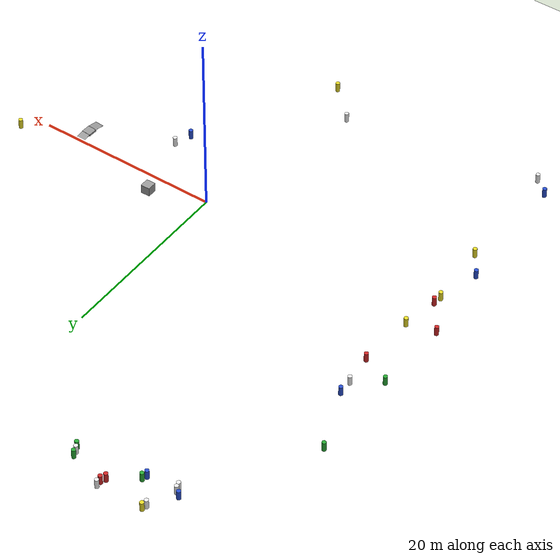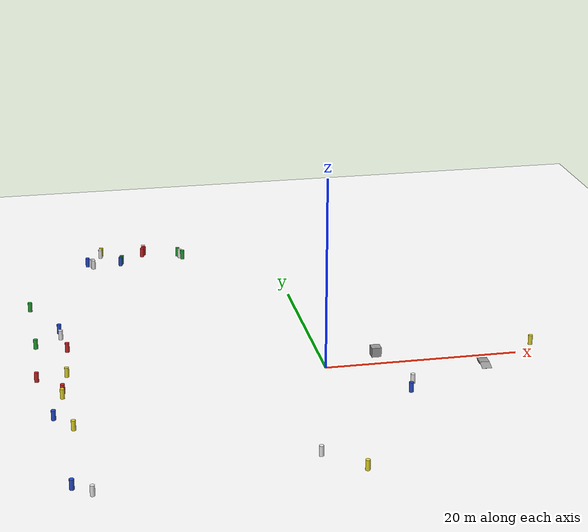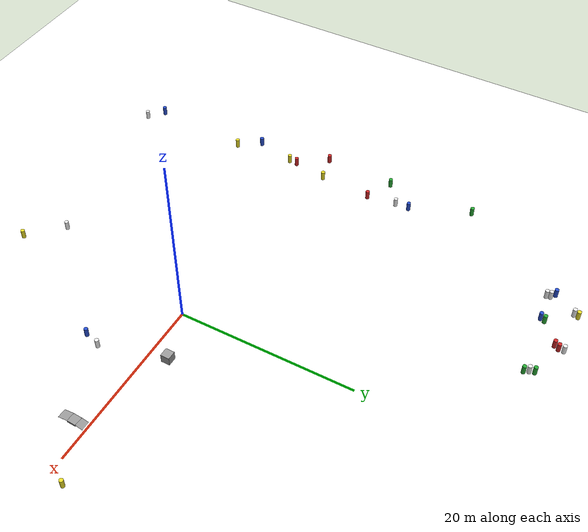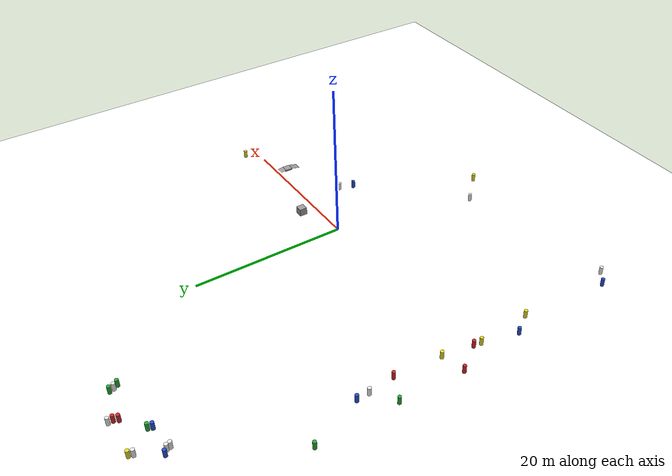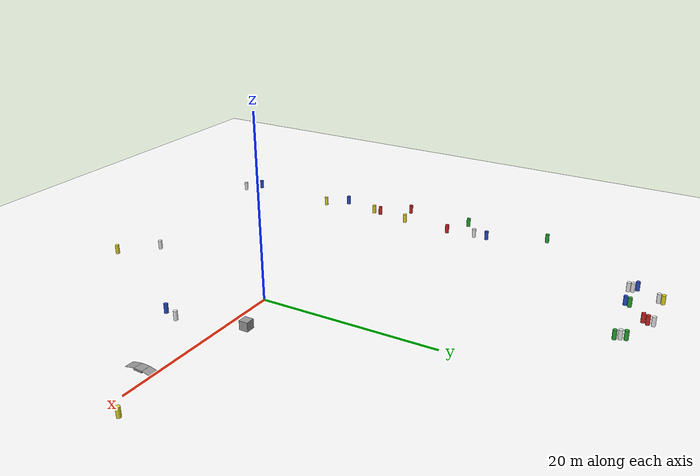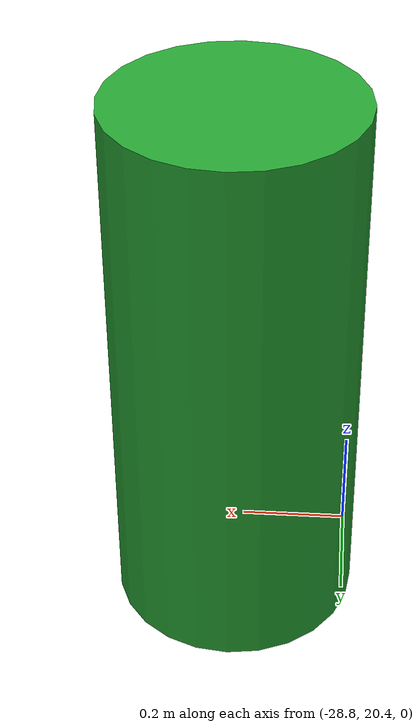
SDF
<sdf version="1.10">
 <world name="IGVC_AutoNav">
  <plugin name="gz::sim::systems::Physics" filename="gz-sim-physics-system"/>
  <plugin name="gz::sim::systems::UserCommands" filename="gz-sim-user-commands-system"/>
  <plugin name="gz::sim::systems::SceneBroadcaster" filename="gz-sim-scene-broadcaster-system"/>
  <plugin name="gz::sim::systems::Contact" filename="gz-sim-contact-system"/>
  <plugin name="gz::sim::systems::NavSat" filename="gz-sim-navsat-system"/>
  <spherical_coordinates>
   <surface_model>EARTH_WGS84</surface_model>
   <world_frame_orientation>ENU</world_frame_orientation>
   <latitude_deg>47.478949999999998</latitude_deg>
   <longitude_deg>19.057784999999999</longitude_deg>
   <elevation>0</elevation>
   <heading_deg>0</heading_deg>
  </spherical_coordinates>
  <plugin name="gz::sim::systems::Sensors" filename="gz-sim-sensors-system">
   <render_engine>ogre2</render_engine>
  </plugin>
  <plugin name="gz::sim::systems::Imu" filename="gz-sim-imu-system"/>
  <plugin name="gz::sim::systems::NavSat" filename="gz-sim-navsat-system"/>
  <gravity>0 0 -9.8000000000000007</gravity>
  <magnetic_field>6.0000000000000002e-06 2.3e-05 -4.1999999999999998e-05</magnetic_field>
  <atmosphere type="adiabatic"/>
  <physics type="ode">
   <max_step_size>0.001</max_step_size>
   <real_time_factor>1</real_time_factor>
   <real_time_update_rate>1000</real_time_update_rate>
  </physics>
  <scene>
   <ambient>0.400000006 0.400000006 0.400000006 1</ambient>
   <background>0.699999988 0.699999988 0.699999988 1</background>
   <shadows>true</shadows>
  </scene>
  <spherical_coordinates>
   <surface_model>EARTH_WGS84</surface_model>
   <latitude_deg>0</latitude_deg>
   <longitude_deg>0</longitude_deg>
   <elevation>0</elevation>
   <heading_deg>0</heading_deg>
  </spherical_coordinates>
  <model name="autonav_ground_plane">
   <static>true</static>
   <link name="link">
    <collision name="collision">
     <geometry><plane><normal>0 0 1</normal><size>64.748999999999995 67.341999999999999</size></plane></geometry>
     <surface><friction><ode><mu>100</mu><mu2>50</mu2></ode></friction></surface>
    </collision>
    <visual name="visual">
     <cast_shadows>false</cast_shadows>
     <geometry><plane><normal>0 0 1</normal><size>64.748999999999995 67.341999999999999</size></plane></geometry>
     <material>
      <diffuse>1 1 1 1</diffuse>
      <specular>1 1 1 1</specular>
      <pbr><metal><albedo_map>file://media/materials/textures/asphalt_autonav.png</albedo_map></metal></pbr>
     </material>
    </visual>
    <inertial>
     <mass>1</mass>
     <inertia><ixx>1</ixx><ixy>0</ixy><ixz>0</ixz><iyy>1</iyy><iyz>0</iyz><izz>1</izz></inertia>
    </inertial>
   </link>
   <pose>0.15136399865150452 7.0954899787902832 0 0 0 0</pose>
  </model>
  <model name="barrel">
   <link name="link">
    <inertial>
     <mass>1</mass>
     <inertia>
      <ixx>0.14583299999999999</ixx>
      <ixy>0</ixy>
      <ixz>0</ixz>
      <iyy>0.14583299999999999</iyy>
      <iyz>0</iyz>
      <izz>0.125</izz>
     </inertia>
    </inertial>
    <visual name="visual">
     <geometry><cylinder><radius>0.222916</radius><length>1.0356700000000001</length></cylinder></geometry>
     <material>
      <script><name>Gazebo/Blue</name><uri>file://media/materials/scripts/gazebo.material</uri></script>
      <shader type="pixel"/>
     </material>
    </visual>
    <collision name="collision">
     <geometry><cylinder><radius>0.222916</radius><length>1.0356700000000001</length></cylinder></geometry>
     <surface>
      <friction>
       <ode><mu>1</mu><mu2>1</mu2><fdir1>0 0 0</fdir1><slip1>0</slip1><slip2>0</slip2></ode>
       <torsional>
        <coefficient>1</coefficient>
        <patch_radius>0</patch_radius>
        <surface_radius>0</surface_radius>
        <use_patch_radius>true</use_patch_radius>
        <ode><slip>0</slip></ode>
       </torsional>
      </friction>
      <bounce><restitution_coefficient>0</restitution_coefficient><threshold>1000000</threshold></bounce>
      <contact>
       <collide_without_contact>false</collide_without_contact>
       <collide_without_contact_bitmask>1</collide_without_contact_bitmask>
       <collide_bitmask>1</collide_bitmask>
       <ode>
        <soft_cfm>0</soft_cfm>
        <soft_erp>0.20000000000000001</soft_erp>
        <kp>10000000000000</kp>
        <kd>1</kd>
        <max_vel>0.01</max_vel>
        <min_depth>0</min_depth>
       </ode>
       <bullet>
        <split_impulse>true</split_impulse>
        <split_impulse_penetration_threshold>-0.01</split_impulse_penetration_threshold>
        <soft_cfm>0</soft_cfm>
        <soft_erp>0.20000000000000001</soft_erp>
        <kp>10000000000000</kp>
        <kd>1</kd>
       </bullet>
      </contact>
     </surface>
    </collision>
   </link>
   <static>false</static>
   <pose>7.06515 -6.9198300000000001 0.49141257691081081 -3.6833131350659278e-18 1.3654958281665594e-16 1.0024447440797465e-17</pose>
  </model>
  <model name="barrel_0">
   <link name="link">
    <inertial>
     <mass>1</mass>
     <inertia>
      <ixx>0.14583299999999999</ixx>
      <ixy>0</ixy>
      <ixz>0</ixz>
      <iyy>0.14583299999999999</iyy>
      <iyz>0</iyz>
      <izz>0.125</izz>
     </inertia>
    </inertial>
    <visual name="visual">
     <geometry><cylinder><radius>0.222916</radius><length>1.0356700000000001</length></cylinder></geometry>
     <material>
      <script><name>Gazebo/Green</name><uri>file://media/materials/scripts/gazebo.material</uri></script>
      <shader type="pixel"/>
     </material>
    </visual>
    <collision name="collision">
     <geometry><cylinder><radius>0.222916</radius><length>1.0356700000000001</length></cylinder></geometry>
     <surface>
      <friction>
       <ode><mu>1</mu><mu2>1</mu2><fdir1>0 0 0</fdir1><slip1>0</slip1><slip2>0</slip2></ode>
       <torsional>
        <coefficient>1</coefficient>
        <patch_radius>0</patch_radius>
        <surface_radius>0</surface_radius>
        <use_patch_radius>true</use_patch_radius>
        <ode><slip>0</slip></ode>
       </torsional>
      </friction>
      <bounce><restitution_coefficient>0</restitution_coefficient><threshold>1000000</threshold></bounce>
      <contact>
       <collide_without_contact>false</collide_without_contact>
       <collide_without_contact_bitmask>1</collide_without_contact_bitmask>
       <collide_bitmask>1</collide_bitmask>
       <ode>
        <soft_cfm>0</soft_cfm>
        <soft_erp>0.20000000000000001</soft_erp>
        <kp>10000000000000</kp>
        <kd>1</kd>
        <max_vel>0.01</max_vel>
        <min_depth>0</min_depth>
       </ode>
       <bullet>
        <split_impulse>true</split_impulse>
        <split_impulse_penetration_threshold>-0.01</split_impulse_penetration_threshold>
        <soft_cfm>0</soft_cfm>
        <soft_erp>0.20000000000000001</soft_erp>
        <kp>10000000000000</kp>
        <kd>1</kd>
       </bullet>
      </contact>
     </surface>
    </collision>
   </link>
   <static>false</static>
   <pose>-10.530400276184082 34.562625885009766 0.48958452317623902 -1.4886732127141289e-06 -6.1759990028397762e-07 2.569076395842905e-12</pose>
  </model>
  <model name="barrel_3">
   <link name="link">
    <inertial>
     <mass>1</mass>
     <inertia>
      <ixx>0.14583299999999999</ixx>
      <ixy>0</ixy>
      <ixz>0</ixz>
      <iyy>0.14583299999999999</iyy>
      <iyz>0</iyz>
      <izz>0.125</izz>
     </inertia>
    </inertial>
    <visual name="visual">
     <geometry><cylinder><radius>0.222916</radius><length>1.0356700000000001</length></cylinder></geometry>
     <material>
      <script><name>Gazebo/White</name><uri>file://media/materials/scripts/gazebo.material</uri></script>
      <shader type="pixel"/>
     </material>
    </visual>
    <collision name="collision">
     <geometry><cylinder><radius>0.222916</radius><length>1.0356700000000001</length></cylinder></geometry>
     <surface>
      <friction>
       <ode><mu>1</mu><mu2>1</mu2><fdir1>0 0 0</fdir1><slip1>0</slip1><slip2>0</slip2></ode>
       <torsional>
        <coefficient>1</coefficient>
        <patch_radius>0</patch_radius>
        <surface_radius>0</surface_radius>
        <use_patch_radius>true</use_patch_radius>
        <ode><slip>0</slip></ode>
       </torsional>
      </friction>
      <bounce><restitution_coefficient>0</restitution_coefficient><threshold>1000000</threshold></bounce>
      <contact>
       <collide_without_contact>false</collide_without_contact>
       <collide_without_contact_bitmask>1</collide_without_contact_bitmask>
       <collide_bitmask>1</collide_bitmask>
       <ode>
        <soft_cfm>0</soft_cfm>
        <soft_erp>0.20000000000000001</soft_erp>
        <kp>10000000000000</kp>
        <kd>1</kd>
        <max_vel>0.01</max_vel>
        <min_depth>0</min_depth>
       </ode>
       <bullet>
        <split_impulse>true</split_impulse>
        <split_impulse_penetration_threshold>-0.01</split_impulse_penetration_threshold>
        <soft_cfm>0</soft_cfm>
        <soft_erp>0.20000000000000001</soft_erp>
        <kp>10000000000000</kp>
        <kd>1</kd>
       </bullet>
      </contact>
     </surface>
    </collision>
   </link>
   <static>false</static>
   <pose>-20.715999094781456 32.180349678920926 0.4894703576685222 2.4689296180203354e-06 1.4035941080635078e-06 -3.2449627405396524e-10</pose>
  </model>
  <model name="barrel_4">
   <link name="link">
    <inertial>
     <mass>1</mass>
     <inertia>
      <ixx>0.14583299999999999</ixx>
      <ixy>0</ixy>
      <ixz>0</ixz>
      <iyy>0.14583299999999999</iyy>
      <iyz>0</iyz>
      <izz>0.125</izz>
     </inertia>
    </inertial>
    <visual name="visual">
     <geometry><cylinder><radius>0.222916</radius><length>1.0356700000000001</length></cylinder></geometry>
     <material>
      <script><name>Gazebo/White</name><uri>file://media/materials/scripts/gazebo.material</uri></script>
      <shader type="pixel"/>
     </material>
    </visual>
    <collision name="collision">
     <geometry><cylinder><radius>0.222916</radius><length>1.0356700000000001</length></cylinder></geometry>
     <surface>
      <friction>
       <ode><mu>1</mu><mu2>1</mu2><fdir1>0 0 0</fdir1><slip1>0</slip1><slip2>0</slip2></ode>
       <torsional>
        <coefficient>1</coefficient>
        <patch_radius>0</patch_radius>
        <surface_radius>0</surface_radius>
        <use_patch_radius>true</use_patch_radius>
        <ode><slip>0</slip></ode>
       </torsional>
      </friction>
      <bounce><restitution_coefficient>0</restitution_coefficient><threshold>1000000</threshold></bounce>
      <contact>
       <collide_without_contact>false</collide_without_contact>
       <collide_without_contact_bitmask>1</collide_without_contact_bitmask>
       <collide_bitmask>1</collide_bitmask>
       <ode>
        <soft_cfm>0</soft_cfm>
        <soft_erp>0.20000000000000001</soft_erp>
        <kp>10000000000000</kp>
        <kd>1</kd>
        <max_vel>0.01</max_vel>
        <min_depth>0</min_depth>
       </ode>
       <bullet>
        <split_impulse>true</split_impulse>
        <split_impulse_penetration_threshold>-0.01</split_impulse_penetration_threshold>
        <soft_cfm>0</soft_cfm>
        <soft_erp>0.20000000000000001</soft_erp>
        <kp>10000000000000</kp>
        <kd>1</kd>
       </bullet>
      </contact>
     </surface>
    </collision>
   </link>
   <static>false</static>
   <pose>-25.243345260620117 -21.755100250244141 0.49008557272004905 -9.7148401091946667e-17 -2.0603843975832751e-16 -1.0068840513921337e-17</pose>
  </model>
  <model name="barrel_5">
   <link name="link">
    <inertial>
     <mass>1</mass>
     <inertia>
      <ixx>0.14583299999999999</ixx>
      <ixy>0</ixy>
      <ixz>0</ixz>
      <iyy>0.14583299999999999</iyy>
      <iyz>0</iyz>
      <izz>0.125</izz>
     </inertia>
    </inertial>
    <visual name="visual">
     <geometry><cylinder><radius>0.222916</radius><length>1.0356700000000001</length></cylinder></geometry>
     <material>
      <script><name>Gazebo/Yellow</name><uri>file://media/materials/scripts/gazebo.material</uri></script>
      <shader type="pixel"/>
     </material>
    </visual>
    <collision name="collision">
     <geometry><cylinder><radius>0.222916</radius><length>1.0356700000000001</length></cylinder></geometry>
     <surface>
      <friction>
       <ode><mu>1</mu><mu2>1</mu2><fdir1>0 0 0</fdir1><slip1>0</slip1><slip2>0</slip2></ode>
       <torsional>
        <coefficient>1</coefficient>
        <patch_radius>0</patch_radius>
        <surface_radius>0</surface_radius>
        <use_patch_radius>true</use_patch_radius>
        <ode><slip>0</slip></ode>
       </torsional>
      </friction>
      <bounce><restitution_coefficient>0</restitution_coefficient><threshold>1000000</threshold></bounce>
      <contact>
       <collide_without_contact>false</collide_without_contact>
       <collide_without_contact_bitmask>1</collide_without_contact_bitmask>
       <collide_bitmask>1</collide_bitmask>
       <ode>
        <soft_cfm>0</soft_cfm>
        <soft_erp>0.20000000000000001</soft_erp>
        <kp>10000000000000</kp>
        <kd>1</kd>
        <max_vel>0.01</max_vel>
        <min_depth>0</min_depth>
       </ode>
       <bullet>
        <split_impulse>true</split_impulse>
        <split_impulse_penetration_threshold>-0.01</split_impulse_penetration_threshold>
        <soft_cfm>0</soft_cfm>
        <soft_erp>0.20000000000000001</soft_erp>
        <kp>10000000000000</kp>
        <kd>1</kd>
       </bullet>
      </contact>
     </surface>
    </collision>
   </link>
   <static>false</static>
   <pose>-25.960578918457031 -8.9916601181030273 0.49093359209623189 8.4803512552871148e-17 -6.8350313958458525e-17 -2.3129656936195062e-17</pose>
  </model>
  <model name="barrel_7">
   <link name="link">
    <inertial>
     <mass>1</mass>
     <inertia>
      <ixx>0.14583299999999999</ixx>
      <ixy>0</ixy>
      <ixz>0</ixz>
      <iyy>0.14583299999999999</iyy>
      <iyz>0</iyz>
      <izz>0.125</izz>
     </inertia>
    </inertial>
    <visual name="visual">
     <geometry><cylinder><radius>0.222916</radius><length>1.0356700000000001</length></cylinder></geometry>
     <material>
      <script><name>Gazebo/Blue</name><uri>file://media/materials/scripts/gazebo.material</uri></script>
      <shader type="pixel"/>
     </material>
    </visual>
    <collision name="collision">
     <geometry><cylinder><radius>0.222916</radius><length>1.0356700000000001</length></cylinder></geometry>
     <surface>
      <friction>
       <ode><mu>1</mu><mu2>1</mu2><fdir1>0 0 0</fdir1><slip1>0</slip1><slip2>0</slip2></ode>
       <torsional>
        <coefficient>1</coefficient>
        <patch_radius>0</patch_radius>
        <surface_radius>0</surface_radius>
        <use_patch_radius>true</use_patch_radius>
        <ode><slip>0</slip></ode>
       </torsional>
      </friction>
      <bounce><restitution_coefficient>0</restitution_coefficient><threshold>1000000</threshold></bounce>
      <contact>
       <collide_without_contact>false</collide_without_contact>
       <collide_without_contact_bitmask>1</collide_without_contact_bitmask>
       <collide_bitmask>1</collide_bitmask>
       <ode>
        <soft_cfm>0</soft_cfm>
        <soft_erp>0.20000000000000001</soft_erp>
        <kp>10000000000000</kp>
        <kd>1</kd>
        <max_vel>0.01</max_vel>
        <min_depth>0</min_depth>
       </ode>
       <bullet>
        <split_impulse>true</split_impulse>
        <split_impulse_penetration_threshold>-0.01</split_impulse_penetration_threshold>
        <soft_cfm>0</soft_cfm>
        <soft_erp>0.20000000000000001</soft_erp>
        <kp>10000000000000</kp>
        <kd>1</kd>
       </bullet>
      </contact>
     </surface>
    </collision>
   </link>
   <static>false</static>
   <pose>-27.665267944335938 -6.5483798980712891 0.49079157449359467 -3.6671660500720249e-16 -2.0048663424014753e-16 -9.7129218591577263e-19</pose>
  </model>
  <model name="barrel_8">
   <link name="link">
    <inertial>
     <mass>1</mass>
     <inertia>
      <ixx>0.14583299999999999</ixx>
      <ixy>0</ixy>
      <ixz>0</ixz>
      <iyy>0.14583299999999999</iyy>
      <iyz>0</iyz>
      <izz>0.125</izz>
     </inertia>
    </inertial>
    <visual name="visual">
     <geometry><cylinder><radius>0.222916</radius><length>1.0356700000000001</length></cylinder></geometry>
     <material>
      <script><name>Gazebo/White</name><uri>file://media/materials/scripts/gazebo.material</uri></script>
      <shader type="pixel"/>
     </material>
    </visual>
    <collision name="collision">
     <geometry><cylinder><radius>0.222916</radius><length>1.0356700000000001</length></cylinder></geometry>
     <surface>
      <friction>
       <ode><mu>1</mu><mu2>1</mu2><fdir1>0 0 0</fdir1><slip1>0</slip1><slip2>0</slip2></ode>
       <torsional>
        <coefficient>1</coefficient>
        <patch_radius>0</patch_radius>
        <surface_radius>0</surface_radius>
        <use_patch_radius>true</use_patch_radius>
        <ode><slip>0</slip></ode>
       </torsional>
      </friction>
      <bounce><restitution_coefficient>0</restitution_coefficient><threshold>1000000</threshold></bounce>
      <contact>
       <collide_without_contact>false</collide_without_contact>
       <collide_without_contact_bitmask>1</collide_without_contact_bitmask>
       <collide_bitmask>1</collide_bitmask>
       <ode>
        <soft_cfm>0</soft_cfm>
        <soft_erp>0.20000000000000001</soft_erp>
        <kp>10000000000000</kp>
        <kd>1</kd>
        <max_vel>0.01</max_vel>
        <min_depth>0</min_depth>
       </ode>
       <bullet>
        <split_impulse>true</split_impulse>
        <split_impulse_penetration_threshold>-0.01</split_impulse_penetration_threshold>
        <soft_cfm>0</soft_cfm>
        <soft_erp>0.20000000000000001</soft_erp>
        <kp>10000000000000</kp>
        <kd>1</kd>
       </bullet>
      </contact>
     </surface>
    </collision>
   </link>
   <static>false</static>
   <pose>-4.3687233924865723 -18.289100646972656 0.48864658578690207 4.100378868644601e-19 -8.0240721352492748e-18 1.3332865833657565e-17</pose>
  </model>
  <model name="barrel_10">
   <link name="link">
    <inertial>
     <mass>1</mass>
     <inertia>
      <ixx>0.14583299999999999</ixx>
      <ixy>0</ixy>
      <ixz>0</ixz>
      <iyy>0.14583299999999999</iyy>
      <iyz>0</iyz>
      <izz>0.125</izz>
     </inertia>
    </inertial>
    <visual name="visual">
     <geometry><cylinder><radius>0.222916</radius><length>1.0356700000000001</length></cylinder></geometry>
     <material>
      <script><name>Gazebo/Blue</name><uri>file://media/materials/scripts/gazebo.material</uri></script>
      <shader type="pixel"/>
     </material>
    </visual>
    <collision name="collision">
     <geometry><cylinder><radius>0.222916</radius><length>1.0356700000000001</length></cylinder></geometry>
     <surface>
      <friction>
       <ode><mu>1</mu><mu2>1</mu2><fdir1>0 0 0</fdir1><slip1>0</slip1><slip2>0</slip2></ode>
       <torsional>
        <coefficient>1</coefficient>
        <patch_radius>0</patch_radius>
        <surface_radius>0</surface_radius>
        <use_patch_radius>true</use_patch_radius>
        <ode><slip>0</slip></ode>
       </torsional>
      </friction>
      <bounce><restitution_coefficient>0</restitution_coefficient><threshold>1000000</threshold></bounce>
      <contact>
       <collide_without_contact>false</collide_without_contact>
       <collide_without_contact_bitmask>1</collide_without_contact_bitmask>
       <collide_bitmask>1</collide_bitmask>
       <ode>
        <soft_cfm>0</soft_cfm>
        <soft_erp>0.20000000000000001</soft_erp>
        <kp>10000000000000</kp>
        <kd>1</kd>
        <max_vel>0.01</max_vel>
        <min_depth>0</min_depth>
       </ode>
       <bullet>
        <split_impulse>true</split_impulse>
        <split_impulse_penetration_threshold>-0.01</split_impulse_penetration_threshold>
        <soft_cfm>0</soft_cfm>
        <soft_erp>0.20000000000000001</soft_erp>
        <kp>10000000000000</kp>
        <kd>1</kd>
       </bullet>
      </contact>
     </surface>
    </collision>
   </link>
   <static>false</static>
   <pose>-25.850784301757812 13.89840030670166 0.49065263426612393 8.4855848883399135e-17 -2.8281407959043097e-17 -2.4067787378642781e-17</pose>
  </model>
  <model name="barrel_11">
   <link name="link">
    <inertial>
     <mass>1</mass>
     <inertia>
      <ixx>0.14583299999999999</ixx>
      <ixy>0</ixy>
      <ixz>0</ixz>
      <iyy>0.14583299999999999</iyy>
      <iyz>0</iyz>
      <izz>0.125</izz>
     </inertia>
    </inertial>
    <visual name="visual">
     <geometry><cylinder><radius>0.222916</radius><length>1.0356700000000001</length></cylinder></geometry>
     <material>
      <script><name>Gazebo/Yellow</name><uri>file://media/materials/scripts/gazebo.material</uri></script>
      <shader type="pixel"/>
     </material>
    </visual>
    <collision name="collision">
     <geometry><cylinder><radius>0.222916</radius><length>1.0356700000000001</length></cylinder></geometry>
     <surface>
      <friction>
       <ode><mu>1</mu><mu2>1</mu2><fdir1>0 0 0</fdir1><slip1>0</slip1><slip2>0</slip2></ode>
       <torsional>
        <coefficient>1</coefficient>
        <patch_radius>0</patch_radius>
        <surface_radius>0</surface_radius>
        <use_patch_radius>true</use_patch_radius>
        <ode><slip>0</slip></ode>
       </torsional>
      </friction>
      <bounce><restitution_coefficient>0</restitution_coefficient><threshold>1000000</threshold></bounce>
      <contact>
       <collide_without_contact>false</collide_without_contact>
       <collide_without_contact_bitmask>1</collide_without_contact_bitmask>
       <collide_bitmask>1</collide_bitmask>
       <ode>
        <soft_cfm>0</soft_cfm>
        <soft_erp>0.20000000000000001</soft_erp>
        <kp>10000000000000</kp>
        <kd>1</kd>
        <max_vel>0.01</max_vel>
        <min_depth>0</min_depth>
       </ode>
       <bullet>
        <split_impulse>true</split_impulse>
        <split_impulse_penetration_threshold>-0.01</split_impulse_penetration_threshold>
        <soft_cfm>0</soft_cfm>
        <soft_erp>0.20000000000000001</soft_erp>
        <kp>10000000000000</kp>
        <kd>1</kd>
       </bullet>
      </contact>
     </surface>
    </collision>
   </link>
   <static>false</static>
   <pose>-26.542016983032227 -2.0249800682067871 0.48987001040062333 -1.2867676321097474e-16 8.4994269969485822e-17 -8.2203599658712203e-18</pose>
  </model>
  <model name="barrel_13">
   <link name="link">
    <inertial>
     <mass>1</mass>
     <inertia>
      <ixx>0.14583299999999999</ixx>
      <ixy>0</ixy>
      <ixz>0</ixz>
      <iyy>0.14583299999999999</iyy>
      <iyz>0</iyz>
      <izz>0.125</izz>
     </inertia>
    </inertial>
    <visual name="visual">
     <geometry><cylinder><radius>0.222916</radius><length>1.0356700000000001</length></cylinder></geometry>
     <material>
      <script><name>Gazebo/Green</name><uri>file://media/materials/scripts/gazebo.material</uri></script>
      <shader type="pixel"/>
     </material>
    </visual>
    <collision name="collision">
     <geometry><cylinder><radius>0.222916</radius><length>1.0356700000000001</length></cylinder></geometry>
     <surface>
      <friction>
       <ode><mu>1</mu><mu2>1</mu2><fdir1>0 0 0</fdir1><slip1>0</slip1><slip2>0</slip2></ode>
       <torsional>
        <coefficient>1</coefficient>
        <patch_radius>0</patch_radius>
        <surface_radius>0</surface_radius>
        <use_patch_radius>true</use_patch_radius>
        <ode><slip>0</slip></ode>
       </torsional>
      </friction>
      <bounce><restitution_coefficient>0</restitution_coefficient><threshold>1000000</threshold></bounce>
      <contact>
       <collide_without_contact>false</collide_without_contact>
       <collide_without_contact_bitmask>1</collide_without_contact_bitmask>
       <collide_bitmask>1</collide_bitmask>
       <ode>
        <soft_cfm>0</soft_cfm>
        <soft_erp>0.20000000000000001</soft_erp>
        <kp>10000000000000</kp>
        <kd>1</kd>
        <max_vel>0.01</max_vel>
        <min_depth>0</min_depth>
       </ode>
       <bullet>
        <split_impulse>true</split_impulse>
        <split_impulse_penetration_threshold>-0.01</split_impulse_penetration_threshold>
        <soft_cfm>0</soft_cfm>
        <soft_erp>0.20000000000000001</soft_erp>
        <kp>10000000000000</kp>
        <kd>1</kd>
       </bullet>
      </contact>
     </surface>
    </collision>
   </link>
   <static>false</static>
   <pose>-28.592302322387695 20.560400009155273 0.49044655962447092 9.8842767419569371e-17 8.5512414983428194e-17 -8.4527958029897826e-18</pose>
  </model>
  <model name="barrel_14">
   <link name="link">
    <inertial>
     <mass>1</mass>
     <inertia>
      <ixx>0.14583299999999999</ixx>
      <ixy>0</ixy>
      <ixz>0</ixz>
      <iyy>0.14583299999999999</iyy>
      <iyz>0</iyz>
      <izz>0.125</izz>
     </inertia>
    </inertial>
    <visual name="visual">
     <geometry><cylinder><radius>0.222916</radius><length>1.0356700000000001</length></cylinder></geometry>
     <material>
      <script><name>Gazebo/Red</name><uri>file://media/materials/scripts/gazebo.material</uri></script>
      <shader type="pixel"/>
     </material>
    </visual>
    <collision name="collision">
     <geometry><cylinder><radius>0.222916</radius><length>1.0356700000000001</length></cylinder></geometry>
     <surface>
      <friction>
       <ode><mu>1</mu><mu2>1</mu2><fdir1>0 0 0</fdir1><slip1>0</slip1><slip2>0</slip2></ode>
       <torsional>
        <coefficient>1</coefficient>
        <patch_radius>0</patch_radius>
        <surface_radius>0</surface_radius>
        <use_patch_radius>true</use_patch_radius>
        <ode><slip>0</slip></ode>
       </torsional>
      </friction>
      <bounce><restitution_coefficient>0</restitution_coefficient><threshold>1000000</threshold></bounce>
      <contact>
       <collide_without_contact>false</collide_without_contact>
       <collide_without_contact_bitmask>1</collide_without_contact_bitmask>
       <collide_bitmask>1</collide_bitmask>
       <ode>
        <soft_cfm>0</soft_cfm>
        <soft_erp>0.20000000000000001</soft_erp>
        <kp>10000000000000</kp>
        <kd>1</kd>
        <max_vel>0.01</max_vel>
        <min_depth>0</min_depth>
       </ode>
       <bullet>
        <split_impulse>true</split_impulse>
        <split_impulse_penetration_threshold>-0.01</split_impulse_penetration_threshold>
        <soft_cfm>0</soft_cfm>
        <soft_erp>0.20000000000000001</soft_erp>
        <kp>10000000000000</kp>
        <kd>1</kd>
       </bullet>
      </contact>
     </surface>
    </collision>
   </link>
   <static>false</static>
   <pose>-25.332365036010742 8.9310302734375 0.49067056502060691 9.6709084724968985e-17 -7.6320325170465179e-17 5.422030205735455e-18</pose>
  </model>
  <model name="barrel_15">
   <link name="link">
    <inertial>
     <mass>1</mass>
     <inertia>
      <ixx>0.14583299999999999</ixx>
      <ixy>0</ixy>
      <ixz>0</ixz>
      <iyy>0.14583299999999999</iyy>
      <iyz>0</iyz>
      <izz>0.125</izz>
     </inertia>
    </inertial>
    <visual name="visual">
     <geometry><cylinder><radius>0.222916</radius><length>1.0356700000000001</length></cylinder></geometry>
     <material>
      <script><name>Gazebo/White</name><uri>file://media/materials/scripts/gazebo.material</uri></script>
      <shader type="pixel"/>
     </material>
    </visual>
    <collision name="collision">
     <geometry><cylinder><radius>0.222916</radius><length>1.0356700000000001</length></cylinder></geometry>
     <surface>
      <friction>
       <ode><mu>1</mu><mu2>1</mu2><fdir1>0 0 0</fdir1><slip1>0</slip1><slip2>0</slip2></ode>
       <torsional>
        <coefficient>1</coefficient>
        <patch_radius>0</patch_radius>
        <surface_radius>0</surface_radius>
        <use_patch_radius>true</use_patch_radius>
        <ode><slip>0</slip></ode>
       </torsional>
      </friction>
      <bounce><restitution_coefficient>0</restitution_coefficient><threshold>1000000</threshold></bounce>
      <contact>
       <collide_without_contact>false</collide_without_contact>
       <collide_without_contact_bitmask>1</collide_without_contact_bitmask>
       <collide_bitmask>1</collide_bitmask>
       <ode>
        <soft_cfm>0</soft_cfm>
        <soft_erp>0.20000000000000001</soft_erp>
        <kp>10000000000000</kp>
        <kd>1</kd>
        <max_vel>0.01</max_vel>
        <min_depth>0</min_depth>
       </ode>
       <bullet>
        <split_impulse>true</split_impulse>
        <split_impulse_penetration_threshold>-0.01</split_impulse_penetration_threshold>
        <soft_cfm>0</soft_cfm>
        <soft_erp>0.20000000000000001</soft_erp>
        <kp>10000000000000</kp>
        <kd>1</kd>
       </bullet>
      </contact>
     </surface>
    </collision>
   </link>
   <static>false</static>
   <pose>-25.783918380737305 12.307399749755859 0.49073859093797045 -8.4790698422489546e-17 -9.669244786946456e-17 -2.6998136379775421e-18</pose>
  </model>
  <model name="barrel_16">
   <link name="link">
    <inertial>
     <mass>1</mass>
     <inertia>
      <ixx>0.14583299999999999</ixx>
      <ixy>0</ixy>
      <ixz>0</ixz>
      <iyy>0.14583299999999999</iyy>
      <iyz>0</iyz>
      <izz>0.125</izz>
     </inertia>
    </inertial>
    <visual name="visual">
     <geometry><cylinder><radius>0.222916</radius><length>1.0356700000000001</length></cylinder></geometry>
     <material>
      <script><name>Gazebo/Yellow</name><uri>file://media/materials/scripts/gazebo.material</uri></script>
      <shader type="pixel"/>
     </material>
    </visual>
    <collision name="collision">
     <geometry><cylinder><radius>0.222916</radius><length>1.0356700000000001</length></cylinder></geometry>
     <surface>
      <friction>
       <ode><mu>1</mu><mu2>1</mu2><fdir1>0 0 0</fdir1><slip1>0</slip1><slip2>0</slip2></ode>
       <torsional>
        <coefficient>1</coefficient>
        <patch_radius>0</patch_radius>
        <surface_radius>0</surface_radius>
        <use_patch_radius>true</use_patch_radius>
        <ode><slip>0</slip></ode>
       </torsional>
      </friction>
      <bounce><restitution_coefficient>0</restitution_coefficient><threshold>1000000</threshold></bounce>
      <contact>
       <collide_without_contact>false</collide_without_contact>
       <collide_without_contact_bitmask>1</collide_without_contact_bitmask>
       <collide_bitmask>1</collide_bitmask>
       <ode>
        <soft_cfm>0</soft_cfm>
        <soft_erp>0.20000000000000001</soft_erp>
        <kp>10000000000000</kp>
        <kd>1</kd>
        <max_vel>0.01</max_vel>
        <min_depth>0</min_depth>
       </ode>
       <bullet>
        <split_impulse>true</split_impulse>
        <split_impulse_penetration_threshold>-0.01</split_impulse_penetration_threshold>
        <soft_cfm>0</soft_cfm>
        <soft_erp>0.20000000000000001</soft_erp>
        <kp>10000000000000</kp>
        <kd>1</kd>
       </bullet>
      </contact>
     </surface>
    </collision>
   </link>
   <static>false</static>
   <pose>-25.781974792480469 2.863569974899292 0.49057155326225477 -8.1219256546073404e-17 3.7478138114279507e-17 -2.3832538959433325e-17</pose>
  </model>
  <model name="barrel_22">
   <link name="link">
    <inertial>
     <mass>1</mass>
     <inertia>
      <ixx>0.14583299999999999</ixx>
      <ixy>0</ixy>
      <ixz>0</ixz>
      <iyy>0.14583299999999999</iyy>
      <iyz>0</iyz>
      <izz>0.125</izz>
     </inertia>
    </inertial>
    <visual name="visual">
     <geometry><cylinder><radius>0.222916</radius><length>1.0356700000000001</length></cylinder></geometry>
     <material>
      <script><name>Gazebo/White</name><uri>file://media/materials/scripts/gazebo.material</uri></script>
      <shader type="pixel"/>
     </material>
    </visual>
    <collision name="collision">
     <geometry><cylinder><radius>0.222916</radius><length>1.0356700000000001</length></cylinder></geometry>
     <surface>
      <friction>
       <ode><mu>1</mu><mu2>1</mu2><fdir1>0 0 0</fdir1><slip1>0</slip1><slip2>0</slip2></ode>
       <torsional>
        <coefficient>1</coefficient>
        <patch_radius>0</patch_radius>
        <surface_radius>0</surface_radius>
        <use_patch_radius>true</use_patch_radius>
        <ode><slip>0</slip></ode>
       </torsional>
      </friction>
      <bounce><restitution_coefficient>0</restitution_coefficient><threshold>1000000</threshold></bounce>
      <contact>
       <collide_without_contact>false</collide_without_contact>
       <collide_without_contact_bitmask>1</collide_without_contact_bitmask>
       <collide_bitmask>1</collide_bitmask>
       <ode>
        <soft_cfm>0</soft_cfm>
        <soft_erp>0.20000000000000001</soft_erp>
        <kp>10000000000000</kp>
        <kd>1</kd>
        <max_vel>0.01</max_vel>
        <min_depth>0</min_depth>
       </ode>
       <bullet>
        <split_impulse>true</split_impulse>
        <split_impulse_penetration_threshold>-0.01</split_impulse_penetration_threshold>
        <soft_cfm>0</soft_cfm>
        <soft_erp>0.20000000000000001</soft_erp>
        <kp>10000000000000</kp>
        <kd>1</kd>
       </bullet>
      </contact>
     </surface>
    </collision>
   </link>
   <static>false</static>
   <pose>-14.483590126037598 36.203399658203125 0.49048651766393375 -1.1107967514665701e-16 -2.356607832990749e-16 -1.1145869038604166e-18</pose>
  </model>
  <model name="barrel_23">
   <link name="link">
    <inertial>
     <mass>1</mass>
     <inertia>
      <ixx>0.14583299999999999</ixx>
      <ixy>0</ixy>
      <ixz>0</ixz>
      <iyy>0.14583299999999999</iyy>
      <iyz>0</iyz>
      <izz>0.125</izz>
     </inertia>
    </inertial>
    <visual name="visual">
     <geometry><cylinder><radius>0.222916</radius><length>1.0356700000000001</length></cylinder></geometry>
     <material>
      <script><name>Gazebo/Green</name><uri>file://media/materials/scripts/gazebo.material</uri></script>
      <shader type="pixel"/>
     </material>
    </visual>
    <collision name="collision">
     <geometry><cylinder><radius>0.222916</radius><length>1.0356700000000001</length></cylinder></geometry>
     <surface>
      <friction>
       <ode><mu>1</mu><mu2>1</mu2><fdir1>0 0 0</fdir1><slip1>0</slip1><slip2>0</slip2></ode>
       <torsional>
        <coefficient>1</coefficient>
        <patch_radius>0</patch_radius>
        <surface_radius>0</surface_radius>
        <use_patch_radius>true</use_patch_radius>
        <ode><slip>0</slip></ode>
       </torsional>
      </friction>
      <bounce><restitution_coefficient>0</restitution_coefficient><threshold>1000000</threshold></bounce>
      <contact>
       <collide_without_contact>false</collide_without_contact>
       <collide_without_contact_bitmask>1</collide_without_contact_bitmask>
       <collide_bitmask>1</collide_bitmask>
       <ode>
        <soft_cfm>0</soft_cfm>
        <soft_erp>0.20000000000000001</soft_erp>
        <kp>10000000000000</kp>
        <kd>1</kd>
        <max_vel>0.01</max_vel>
        <min_depth>0</min_depth>
       </ode>
       <bullet>
        <split_impulse>true</split_impulse>
        <split_impulse_penetration_threshold>-0.01</split_impulse_penetration_threshold>
        <soft_cfm>0</soft_cfm>
        <soft_erp>0.20000000000000001</soft_erp>
        <kp>10000000000000</kp>
        <kd>1</kd>
       </bullet>
      </contact>
     </surface>
    </collision>
   </link>
   <static>false</static>
   <pose>-28.489200592041016 10.397676467895508 0.48974604376635594 -1.4178488771199561e-16 -8.5027954482303544e-17 -2.0011433239803875e-17</pose>
  </model>
  <model name="barrel_24">
   <link name="link">
    <inertial>
     <mass>1</mass>
     <inertia>
      <ixx>0.14583299999999999</ixx>
      <ixy>0</ixy>
      <ixz>0</ixz>
      <iyy>0.14583299999999999</iyy>
      <iyz>0</iyz>
      <izz>0.125</izz>
     </inertia>
    </inertial>
    <visual name="visual">
     <geometry><cylinder><radius>0.222916</radius><length>1.0356700000000001</length></cylinder></geometry>
     <material>
      <script><name>Gazebo/White</name><uri>file://media/materials/scripts/gazebo.material</uri></script>
      <shader type="pixel"/>
     </material>
    </visual>
    <collision name="collision">
     <geometry><cylinder><radius>0.222916</radius><length>1.0356700000000001</length></cylinder></geometry>
     <surface>
      <friction>
       <ode><mu>1</mu><mu2>1</mu2><fdir1>0 0 0</fdir1><slip1>0</slip1><slip2>0</slip2></ode>
       <torsional>
        <coefficient>1</coefficient>
        <patch_radius>0</patch_radius>
        <surface_radius>0</surface_radius>
        <use_patch_radius>true</use_patch_radius>
        <ode><slip>0</slip></ode>
       </torsional>
      </friction>
      <bounce><restitution_coefficient>0</restitution_coefficient><threshold>1000000</threshold></bounce>
      <contact>
       <collide_without_contact>false</collide_without_contact>
       <collide_without_contact_bitmask>1</collide_without_contact_bitmask>
       <collide_bitmask>1</collide_bitmask>
       <ode>
        <soft_cfm>0</soft_cfm>
        <soft_erp>0.20000000000000001</soft_erp>
        <kp>10000000000000</kp>
        <kd>1</kd>
        <max_vel>0.01</max_vel>
        <min_depth>0</min_depth>
       </ode>
       <bullet>
        <split_impulse>true</split_impulse>
        <split_impulse_penetration_threshold>-0.01</split_impulse_penetration_threshold>
        <soft_cfm>0</soft_cfm>
        <soft_erp>0.20000000000000001</soft_erp>
        <kp>10000000000000</kp>
        <kd>1</kd>
       </bullet>
      </contact>
     </surface>
    </collision>
   </link>
   <static>false</static>
   <pose>-10.382210333158399 34.021792885617479 0.48974905596310941 2.9772533249613637e-06 1.2353802648623476e-06 -4.6647633560675959e-12</pose>
  </model>
  <model name="barrel_26">
   <link name="link">
    <inertial>
     <mass>1</mass>
     <inertia>
      <ixx>0.14583299999999999</ixx>
      <ixy>0</ixy>
      <ixz>0</ixz>
      <iyy>0.14583299999999999</iyy>
      <iyz>0</iyz>
      <izz>0.125</izz>
     </inertia>
    </inertial>
    <visual name="visual">
     <geometry><cylinder><radius>0.222916</radius><length>1.0356700000000001</length></cylinder></geometry>
     <material>
      <script><name>Gazebo/Red</name><uri>file://media/materials/scripts/gazebo.material</uri></script>
      <shader type="pixel"/>
     </material>
    </visual>
    <collision name="collision">
     <geometry><cylinder><radius>0.222916</radius><length>1.0356700000000001</length></cylinder></geometry>
     <surface>
      <friction>
       <ode><mu>1</mu><mu2>1</mu2><fdir1>0 0 0</fdir1><slip1>0</slip1><slip2>0</slip2></ode>
       <torsional>
        <coefficient>1</coefficient>
        <patch_radius>0</patch_radius>
        <surface_radius>0</surface_radius>
        <use_patch_radius>true</use_patch_radius>
        <ode><slip>0</slip></ode>
       </torsional>
      </friction>
      <bounce><restitution_coefficient>0</restitution_coefficient><threshold>1000000</threshold></bounce>
      <contact>
       <collide_without_contact>false</collide_without_contact>
       <collide_without_contact_bitmask>1</collide_without_contact_bitmask>
       <collide_bitmask>1</collide_bitmask>
       <ode>
        <soft_cfm>0</soft_cfm>
        <soft_erp>0.20000000000000001</soft_erp>
        <kp>10000000000000</kp>
        <kd>1</kd>
        <max_vel>0.01</max_vel>
        <min_depth>0</min_depth>
       </ode>
       <bullet>
        <split_impulse>true</split_impulse>
        <split_impulse_penetration_threshold>-0.01</split_impulse_penetration_threshold>
        <soft_cfm>0</soft_cfm>
        <soft_erp>0.20000000000000001</soft_erp>
        <kp>10000000000000</kp>
        <kd>1</kd>
       </bullet>
      </contact>
     </surface>
    </collision>
   </link>
   <static>false</static>
   <pose>-14.45680046081543 35.6458740234375 0.4894876432278748 -1.9377832968222688e-16 -2.1769077768308592e-16 3.5422885636257805e-17</pose>
  </model>
  <model name="barrel_27">
   <link name="link">
    <inertial>
     <mass>1</mass>
     <inertia>
      <ixx>0.14583299999999999</ixx>
      <ixy>0</ixy>
      <ixz>0</ixz>
      <iyy>0.14583299999999999</iyy>
      <iyz>0</iyz>
      <izz>0.125</izz>
     </inertia>
    </inertial>
    <visual name="visual">
     <geometry><cylinder><radius>0.222916</radius><length>1.0356700000000001</length></cylinder></geometry>
     <material>
      <script><name>Gazebo/Red</name><uri>file://media/materials/scripts/gazebo.material</uri></script>
      <shader type="pixel"/>
     </material>
    </visual>
    <collision name="collision">
     <geometry><cylinder><radius>0.222916</radius><length>1.0356700000000001</length></cylinder></geometry>
     <surface>
      <friction>
       <ode><mu>1</mu><mu2>1</mu2><fdir1>0 0 0</fdir1><slip1>0</slip1><slip2>0</slip2></ode>
       <torsional>
        <coefficient>1</coefficient>
        <patch_radius>0</patch_radius>
        <surface_radius>0</surface_radius>
        <use_patch_radius>true</use_patch_radius>
        <ode><slip>0</slip></ode>
       </torsional>
      </friction>
      <bounce><restitution_coefficient>0</restitution_coefficient><threshold>1000000</threshold></bounce>
      <contact>
       <collide_without_contact>false</collide_without_contact>
       <collide_without_contact_bitmask>1</collide_without_contact_bitmask>
       <collide_bitmask>1</collide_bitmask>
       <ode>
        <soft_cfm>0</soft_cfm>
        <soft_erp>0.20000000000000001</soft_erp>
        <kp>10000000000000</kp>
        <kd>1</kd>
        <max_vel>0.01</max_vel>
        <min_depth>0</min_depth>
       </ode>
       <bullet>
        <split_impulse>true</split_impulse>
        <split_impulse_penetration_threshold>-0.01</split_impulse_penetration_threshold>
        <soft_cfm>0</soft_cfm>
        <soft_erp>0.20000000000000001</soft_erp>
        <kp>10000000000000</kp>
        <kd>1</kd>
       </bullet>
      </contact>
     </surface>
    </collision>
   </link>
   <static>false</static>
   <pose>-14.709400177001953 35.132270812988281 0.49019770585612027 -9.6812229861241691e-17 6.8445163533058854e-17 -2.781063698151175e-18</pose>
  </model>
  <model name="barrel_28">
   <link name="link">
    <inertial>
     <mass>1</mass>
     <inertia>
      <ixx>0.14583299999999999</ixx>
      <ixy>0</ixy>
      <ixz>0</ixz>
      <iyy>0.14583299999999999</iyy>
      <iyz>0</iyz>
      <izz>0.125</izz>
     </inertia>
    </inertial>
    <visual name="visual">
     <geometry><cylinder><radius>0.222916</radius><length>1.0356700000000001</length></cylinder></geometry>
     <material>
      <script><name>Gazebo/White</name><uri>file://media/materials/scripts/gazebo.material</uri></script>
      <shader type="pixel"/>
     </material>
    </visual>
    <collision name="collision">
     <geometry><cylinder><radius>0.222916</radius><length>1.0356700000000001</length></cylinder></geometry>
     <surface>
      <friction>
       <ode><mu>1</mu><mu2>1</mu2><fdir1>0 0 0</fdir1><slip1>0</slip1><slip2>0</slip2></ode>
       <torsional>
        <coefficient>1</coefficient>
        <patch_radius>0</patch_radius>
        <surface_radius>0</surface_radius>
        <use_patch_radius>true</use_patch_radius>
        <ode><slip>0</slip></ode>
       </torsional>
      </friction>
      <bounce><restitution_coefficient>0</restitution_coefficient><threshold>1000000</threshold></bounce>
      <contact>
       <collide_without_contact>false</collide_without_contact>
       <collide_without_contact_bitmask>1</collide_without_contact_bitmask>
       <collide_bitmask>1</collide_bitmask>
       <ode>
        <soft_cfm>0</soft_cfm>
        <soft_erp>0.20000000000000001</soft_erp>
        <kp>10000000000000</kp>
        <kd>1</kd>
        <max_vel>0.01</max_vel>
        <min_depth>0</min_depth>
       </ode>
       <bullet>
        <split_impulse>true</split_impulse>
        <split_impulse_penetration_threshold>-0.01</split_impulse_penetration_threshold>
        <soft_cfm>0</soft_cfm>
        <soft_erp>0.20000000000000001</soft_erp>
        <kp>10000000000000</kp>
        <kd>1</kd>
       </bullet>
      </contact>
     </surface>
    </collision>
   </link>
   <static>false</static>
   <pose>-20.809400871597017 32.616288079071886 0.48859401283302778 -8.9473439844590073e-07 -8.2094106487091804e-07 -4.9537839781682015e-10</pose>
  </model>
  <model name="barrel_30">
   <link name="link">
    <inertial>
     <mass>1</mass>
     <inertia>
      <ixx>0.14583299999999999</ixx>
      <ixy>0</ixy>
      <ixz>0</ixz>
      <iyy>0.14583299999999999</iyy>
      <iyz>0</iyz>
      <izz>0.125</izz>
     </inertia>
    </inertial>
    <visual name="visual">
     <geometry><cylinder><radius>0.222916</radius><length>1.0356700000000001</length></cylinder></geometry>
     <material>
      <script><name>Gazebo/Green</name><uri>file://media/materials/scripts/gazebo.material</uri></script>
      <shader type="pixel"/>
     </material>
    </visual>
    <collision name="collision">
     <geometry><cylinder><radius>0.222916</radius><length>1.0356700000000001</length></cylinder></geometry>
     <surface>
      <friction>
       <ode><mu>1</mu><mu2>1</mu2><fdir1>0 0 0</fdir1><slip1>0</slip1><slip2>0</slip2></ode>
       <torsional>
        <coefficient>1</coefficient>
        <patch_radius>0</patch_radius>
        <surface_radius>0</surface_radius>
        <use_patch_radius>true</use_patch_radius>
        <ode><slip>0</slip></ode>
       </torsional>
      </friction>
      <bounce><restitution_coefficient>0</restitution_coefficient><threshold>1000000</threshold></bounce>
      <contact>
       <collide_without_contact>false</collide_without_contact>
       <collide_without_contact_bitmask>1</collide_without_contact_bitmask>
       <collide_bitmask>1</collide_bitmask>
       <ode>
        <soft_cfm>0</soft_cfm>
        <soft_erp>0.20000000000000001</soft_erp>
        <kp>10000000000000</kp>
        <kd>1</kd>
        <max_vel>0.01</max_vel>
        <min_depth>0</min_depth>
       </ode>
       <bullet>
        <split_impulse>true</split_impulse>
        <split_impulse_penetration_threshold>-0.01</split_impulse_penetration_threshold>
        <soft_cfm>0</soft_cfm>
        <soft_erp>0.20000000000000001</soft_erp>
        <kp>10000000000000</kp>
        <kd>1</kd>
       </bullet>
      </contact>
     </surface>
    </collision>
   </link>
   <static>false</static>
   <pose>-17.321500041087312 33.171632856995899 0.47371694899537009 2.0568781118020949e-06 6.26101729795303e-07 1.7494342082150027e-09</pose>
  </model>
  <model name="barrel_31">
   <link name="link">
    <inertial>
     <mass>1</mass>
     <inertia>
      <ixx>0.14583299999999999</ixx>
      <ixy>0</ixy>
      <ixz>0</ixz>
      <iyy>0.14583299999999999</iyy>
      <iyz>0</iyz>
      <izz>0.125</izz>
     </inertia>
    </inertial>
    <visual name="visual">
     <geometry><cylinder><radius>0.222916</radius><length>1.0356700000000001</length></cylinder></geometry>
     <material>
      <script><name>Gazebo/Green</name><uri>file://media/materials/scripts/gazebo.material</uri></script>
      <shader type="pixel"/>
     </material>
    </visual>
    <collision name="collision">
     <geometry><cylinder><radius>0.222916</radius><length>1.0356700000000001</length></cylinder></geometry>
     <surface>
      <friction>
       <ode><mu>1</mu><mu2>1</mu2><fdir1>0 0 0</fdir1><slip1>0</slip1><slip2>0</slip2></ode>
       <torsional>
        <coefficient>1</coefficient>
        <patch_radius>0</patch_radius>
        <surface_radius>0</surface_radius>
        <use_patch_radius>true</use_patch_radius>
        <ode><slip>0</slip></ode>
       </torsional>
      </friction>
      <bounce><restitution_coefficient>0</restitution_coefficient><threshold>1000000</threshold></bounce>
      <contact>
       <collide_without_contact>false</collide_without_contact>
       <collide_without_contact_bitmask>1</collide_without_contact_bitmask>
       <collide_bitmask>1</collide_bitmask>
       <ode>
        <soft_cfm>0</soft_cfm>
        <soft_erp>0.20000000000000001</soft_erp>
        <kp>10000000000000</kp>
        <kd>1</kd>
        <max_vel>0.01</max_vel>
        <min_depth>0</min_depth>
       </ode>
       <bullet>
        <split_impulse>true</split_impulse>
        <split_impulse_penetration_threshold>-0.01</split_impulse_penetration_threshold>
        <soft_cfm>0</soft_cfm>
        <soft_erp>0.20000000000000001</soft_erp>
        <kp>10000000000000</kp>
        <kd>1</kd>
       </bullet>
      </contact>
     </surface>
    </collision>
   </link>
   <static>false</static>
   <pose>-10.104596138000488 33.534801483154297 0.49020029162394746 -1.2110375568972145e-16 1.4554946602714789e-16 9.1260601091329904e-18</pose>
  </model>
  <model name="barrel_32">
   <link name="link">
    <inertial>
     <mass>1</mass>
     <inertia>
      <ixx>0.14583299999999999</ixx>
      <ixy>0</ixy>
      <ixz>0</ixz>
      <iyy>0.14583299999999999</iyy>
      <iyz>0</iyz>
      <izz>0.125</izz>
     </inertia>
    </inertial>
    <visual name="visual">
     <geometry><cylinder><radius>0.222916</radius><length>1.0356700000000001</length></cylinder></geometry>
     <material>
      <script><name>Gazebo/Yellow</name><uri>file://media/materials/scripts/gazebo.material</uri></script>
      <shader type="pixel"/>
     </material>
    </visual>
    <collision name="collision">
     <geometry><cylinder><radius>0.222916</radius><length>1.0356700000000001</length></cylinder></geometry>
     <surface>
      <friction>
       <ode><mu>1</mu><mu2>1</mu2><fdir1>0 0 0</fdir1><slip1>0</slip1><slip2>0</slip2></ode>
       <torsional>
        <coefficient>1</coefficient>
        <patch_radius>0</patch_radius>
        <surface_radius>0</surface_radius>
        <use_patch_radius>true</use_patch_radius>
        <ode><slip>0</slip></ode>
       </torsional>
      </friction>
      <bounce><restitution_coefficient>0</restitution_coefficient><threshold>1000000</threshold></bounce>
      <contact>
       <collide_without_contact>false</collide_without_contact>
       <collide_without_contact_bitmask>1</collide_without_contact_bitmask>
       <collide_bitmask>1</collide_bitmask>
       <ode>
        <soft_cfm>0</soft_cfm>
        <soft_erp>0.20000000000000001</soft_erp>
        <kp>10000000000000</kp>
        <kd>1</kd>
        <max_vel>0.01</max_vel>
        <min_depth>0</min_depth>
       </ode>
       <bullet>
        <split_impulse>true</split_impulse>
        <split_impulse_penetration_threshold>-0.01</split_impulse_penetration_threshold>
        <soft_cfm>0</soft_cfm>
        <soft_erp>0.20000000000000001</soft_erp>
        <kp>10000000000000</kp>
        <kd>1</kd>
       </bullet>
      </contact>
     </surface>
    </collision>
   </link>
   <static>false</static>
   <pose>-19.487651824951172 36.035198211669922 0.51783401764546333 8.549052785967678e-17 7.0953112783709159e-17 -1.4670973031880027e-19</pose>
  </model>
  <model name="barrel_33">
   <link name="link">
    <inertial>
     <mass>1</mass>
     <inertia>
      <ixx>0.14583299999999999</ixx>
      <ixy>0</ixy>
      <ixz>0</ixz>
      <iyy>0.14583299999999999</iyy>
      <iyz>0</iyz>
      <izz>0.125</izz>
     </inertia>
    </inertial>
    <visual name="visual">
     <geometry><cylinder><radius>0.222916</radius><length>1.0356700000000001</length></cylinder></geometry>
     <material>
      <script><name>Gazebo/White</name><uri>file://media/materials/scripts/gazebo.material</uri></script>
      <shader type="pixel"/>
     </material>
    </visual>
    <collision name="collision">
     <geometry><cylinder><radius>0.222916</radius><length>1.0356700000000001</length></cylinder></geometry>
     <surface>
      <friction>
       <ode><mu>1</mu><mu2>1</mu2><fdir1>0 0 0</fdir1><slip1>0</slip1><slip2>0</slip2></ode>
       <torsional>
        <coefficient>1</coefficient>
        <patch_radius>0</patch_radius>
        <surface_radius>0</surface_radius>
        <use_patch_radius>true</use_patch_radius>
        <ode><slip>0</slip></ode>
       </torsional>
      </friction>
      <bounce><restitution_coefficient>0</restitution_coefficient><threshold>1000000</threshold></bounce>
      <contact>
       <collide_without_contact>false</collide_without_contact>
       <collide_without_contact_bitmask>1</collide_without_contact_bitmask>
       <collide_bitmask>1</collide_bitmask>
       <ode>
        <soft_cfm>0</soft_cfm>
        <soft_erp>0.20000000000000001</soft_erp>
        <kp>10000000000000</kp>
        <kd>1</kd>
        <max_vel>0.01</max_vel>
        <min_depth>0</min_depth>
       </ode>
       <bullet>
        <split_impulse>true</split_impulse>
        <split_impulse_penetration_threshold>-0.01</split_impulse_penetration_threshold>
        <soft_cfm>0</soft_cfm>
        <soft_erp>0.20000000000000001</soft_erp>
        <kp>10000000000000</kp>
        <kd>1</kd>
       </bullet>
      </contact>
     </surface>
    </collision>
   </link>
   <static>false</static>
   <pose>7.7082499999999996 -5.0892799999999996 0.49155457447689382 -2.318817732758174e-16 -3.026701288918057e-17 1.417066782091021e-17</pose>
  </model>
  <model name="barrel_34">
   <link name="link">
    <inertial>
     <mass>1</mass>
     <inertia>
      <ixx>0.14583299999999999</ixx>
      <ixy>0</ixy>
      <ixz>0</ixz>
      <iyy>0.14583299999999999</iyy>
      <iyz>0</iyz>
      <izz>0.125</izz>
     </inertia>
    </inertial>
    <visual name="visual">
     <geometry><cylinder><radius>0.222916</radius><length>1.0356700000000001</length></cylinder></geometry>
     <material>
      <script><name>Gazebo/Blue</name><uri>file://media/materials/scripts/gazebo.material</uri></script>
      <shader type="pixel"/>
     </material>
    </visual>
    <collision name="collision">
     <geometry><cylinder><radius>0.222916</radius><length>1.0356700000000001</length></cylinder></geometry>
     <surface>
      <friction>
       <ode><mu>1</mu><mu2>1</mu2><fdir1>0 0 0</fdir1><slip1>0</slip1><slip2>0</slip2></ode>
       <torsional>
        <coefficient>1</coefficient>
        <patch_radius>0</patch_radius>
        <surface_radius>0</surface_radius>
        <use_patch_radius>true</use_patch_radius>
        <ode><slip>0</slip></ode>
       </torsional>
      </friction>
      <bounce><restitution_coefficient>0</restitution_coefficient><threshold>1000000</threshold></bounce>
      <contact>
       <collide_without_contact>false</collide_without_contact>
       <collide_without_contact_bitmask>1</collide_without_contact_bitmask>
       <collide_bitmask>1</collide_bitmask>
       <ode>
        <soft_cfm>0</soft_cfm>
        <soft_erp>0.20000000000000001</soft_erp>
        <kp>10000000000000</kp>
        <kd>1</kd>
        <max_vel>0.01</max_vel>
        <min_depth>0</min_depth>
       </ode>
       <bullet>
        <split_impulse>true</split_impulse>
        <split_impulse_penetration_threshold>-0.01</split_impulse_penetration_threshold>
        <soft_cfm>0</soft_cfm>
        <soft_erp>0.20000000000000001</soft_erp>
        <kp>10000000000000</kp>
        <kd>1</kd>
       </bullet>
      </contact>
     </surface>
    </collision>
   </link>
   <static>false</static>
   <pose>-17.506099700927734 32.680656433105469 0.47031510963540535 -7.0457700149754715e-07 -6.5627777613392629e-08 1.7966299875048229e-09</pose>
  </model>
  <model name="barrel_35">
   <link name="link">
    <inertial>
     <mass>1</mass>
     <inertia>
      <ixx>0.14583299999999999</ixx>
      <ixy>0</ixy>
      <ixz>0</ixz>
      <iyy>0.14583299999999999</iyy>
      <iyz>0</iyz>
      <izz>0.125</izz>
     </inertia>
    </inertial>
    <visual name="visual">
     <geometry><cylinder><radius>0.222916</radius><length>1.0356700000000001</length></cylinder></geometry>
     <material>
      <script><name>Gazebo/Blue</name><uri>file://media/materials/scripts/gazebo.material</uri></script>
      <shader type="pixel"/>
     </material>
    </visual>
    <collision name="collision">
     <geometry><cylinder><radius>0.222916</radius><length>1.0356700000000001</length></cylinder></geometry>
     <surface>
      <friction>
       <ode><mu>1</mu><mu2>1</mu2><fdir1>0 0 0</fdir1><slip1>0</slip1><slip2>0</slip2></ode>
       <torsional>
        <coefficient>1</coefficient>
        <patch_radius>0</patch_radius>
        <surface_radius>0</surface_radius>
        <use_patch_radius>true</use_patch_radius>
        <ode><slip>0</slip></ode>
       </torsional>
      </friction>
      <bounce><restitution_coefficient>0</restitution_coefficient><threshold>1000000</threshold></bounce>
      <contact>
       <collide_without_contact>false</collide_without_contact>
       <collide_without_contact_bitmask>1</collide_without_contact_bitmask>
       <collide_bitmask>1</collide_bitmask>
       <ode>
        <soft_cfm>0</soft_cfm>
        <soft_erp>0.20000000000000001</soft_erp>
        <kp>10000000000000</kp>
        <kd>1</kd>
        <max_vel>0.01</max_vel>
        <min_depth>0</min_depth>
       </ode>
       <bullet>
        <split_impulse>true</split_impulse>
        <split_impulse_penetration_threshold>-0.01</split_impulse_penetration_threshold>
        <soft_cfm>0</soft_cfm>
        <soft_erp>0.20000000000000001</soft_erp>
        <kp>10000000000000</kp>
        <kd>1</kd>
       </bullet>
      </contact>
     </surface>
    </collision>
   </link>
   <static>false</static>
   <pose>-26.914508819580078 -20.318000793457031 0.49032160755710863 2.0076202450305797e-16 9.6772297827044165e-17 -4.4367139701304541e-18</pose>
  </model>
  <model name="barrel_36">
   <link name="link">
    <inertial>
     <mass>1</mass>
     <inertia>
      <ixx>0.14583299999999999</ixx>
      <ixy>0</ixy>
      <ixz>0</ixz>
      <iyy>0.14583299999999999</iyy>
      <iyz>0</iyz>
      <izz>0.125</izz>
     </inertia>
    </inertial>
    <visual name="visual">
     <geometry><cylinder><radius>0.222916</radius><length>1.0356700000000001</length></cylinder></geometry>
     <material>
      <script><name>Gazebo/Blue</name><uri>file://media/materials/scripts/gazebo.material</uri></script>
      <shader type="pixel"/>
     </material>
    </visual>
    <collision name="collision">
     <geometry><cylinder><radius>0.222916</radius><length>1.0356700000000001</length></cylinder></geometry>
     <surface>
      <friction>
       <ode><mu>1</mu><mu2>1</mu2><fdir1>0 0 0</fdir1><slip1>0</slip1><slip2>0</slip2></ode>
       <torsional>
        <coefficient>1</coefficient>
        <patch_radius>0</patch_radius>
        <surface_radius>0</surface_radius>
        <use_patch_radius>true</use_patch_radius>
        <ode><slip>0</slip></ode>
       </torsional>
      </friction>
      <bounce><restitution_coefficient>0</restitution_coefficient><threshold>1000000</threshold></bounce>
      <contact>
       <collide_without_contact>false</collide_without_contact>
       <collide_without_contact_bitmask>1</collide_without_contact_bitmask>
       <collide_bitmask>1</collide_bitmask>
       <ode>
        <soft_cfm>0</soft_cfm>
        <soft_erp>0.20000000000000001</soft_erp>
        <kp>10000000000000</kp>
        <kd>1</kd>
        <max_vel>0.01</max_vel>
        <min_depth>0</min_depth>
       </ode>
       <bullet>
        <split_impulse>true</split_impulse>
        <split_impulse_penetration_threshold>-0.01</split_impulse_penetration_threshold>
        <soft_cfm>0</soft_cfm>
        <soft_erp>0.20000000000000001</soft_erp>
        <kp>10000000000000</kp>
        <kd>1</kd>
       </bullet>
      </contact>
     </surface>
    </collision>
   </link>
   <static>false</static>
   <pose>-21.336200714111325 33.0107421875 0.4874576545918437 -2.2173742754622149e-07 1.9725783795051446e-08 -2.5545801000671541e-10</pose>
  </model>
  <model name="barrel_37">
   <link name="link">
    <inertial>
     <mass>1</mass>
     <inertia>
      <ixx>0.14583299999999999</ixx>
      <ixy>0</ixy>
      <ixz>0</ixz>
      <iyy>0.14583299999999999</iyy>
      <iyz>0</iyz>
      <izz>0.125</izz>
     </inertia>
    </inertial>
    <visual name="visual">
     <geometry><cylinder><radius>0.222916</radius><length>1.0356700000000001</length></cylinder></geometry>
     <material>
      <script><name>Gazebo/Yellow</name><uri>file://media/materials/scripts/gazebo.material</uri></script>
      <shader type="pixel"/>
     </material>
    </visual>
    <collision name="collision">
     <geometry><cylinder><radius>0.222916</radius><length>1.0356700000000001</length></cylinder></geometry>
     <surface>
      <friction>
       <ode><mu>1</mu><mu2>1</mu2><fdir1>0 0 0</fdir1><slip1>0</slip1><slip2>0</slip2></ode>
       <torsional>
        <coefficient>1</coefficient>
        <patch_radius>0</patch_radius>
        <surface_radius>0</surface_radius>
        <use_patch_radius>true</use_patch_radius>
        <ode><slip>0</slip></ode>
       </torsional>
      </friction>
      <bounce><restitution_coefficient>0</restitution_coefficient><threshold>1000000</threshold></bounce>
      <contact>
       <collide_without_contact>false</collide_without_contact>
       <collide_without_contact_bitmask>1</collide_without_contact_bitmask>
       <collide_bitmask>1</collide_bitmask>
       <ode>
        <soft_cfm>0</soft_cfm>
        <soft_erp>0.20000000000000001</soft_erp>
        <kp>10000000000000</kp>
        <kd>1</kd>
        <max_vel>0.01</max_vel>
        <min_depth>0</min_depth>
       </ode>
       <bullet>
        <split_impulse>true</split_impulse>
        <split_impulse_penetration_threshold>-0.01</split_impulse_penetration_threshold>
        <soft_cfm>0</soft_cfm>
        <soft_erp>0.20000000000000001</soft_erp>
        <kp>10000000000000</kp>
        <kd>1</kd>
       </bullet>
      </contact>
     </surface>
    </collision>
   </link>
   <static>false</static>
   <pose>-0.90059500932693481 -21.695306777954102 0.49056157526459265 -9.5802751048081433e-17 8.4864277923048779e-17 -6.6364206722518004e-18</pose>
  </model>
  <model name="barrel_38">
   <link name="link">
    <inertial>
     <mass>1</mass>
     <inertia>
      <ixx>0.14583299999999999</ixx>
      <ixy>0</ixy>
      <ixz>0</ixz>
      <iyy>0.14583299999999999</iyy>
      <iyz>0</iyz>
      <izz>0.125</izz>
     </inertia>
    </inertial>
    <visual name="visual">
     <geometry><cylinder><radius>0.222916</radius><length>1.0356700000000001</length></cylinder></geometry>
     <material>
      <script><name>Gazebo/White</name><uri>file://media/materials/scripts/gazebo.material</uri></script>
      <shader type="pixel"/>
     </material>
    </visual>
    <collision name="collision">
     <geometry><cylinder><radius>0.222916</radius><length>1.0356700000000001</length></cylinder></geometry>
     <surface>
      <friction>
       <ode><mu>1</mu><mu2>1</mu2><fdir1>0 0 0</fdir1><slip1>0</slip1><slip2>0</slip2></ode>
       <torsional>
        <coefficient>1</coefficient>
        <patch_radius>0</patch_radius>
        <surface_radius>0</surface_radius>
        <use_patch_radius>true</use_patch_radius>
        <ode><slip>0</slip></ode>
       </torsional>
      </friction>
      <bounce><restitution_coefficient>0</restitution_coefficient><threshold>1000000</threshold></bounce>
      <contact>
       <collide_without_contact>false</collide_without_contact>
       <collide_without_contact_bitmask>1</collide_without_contact_bitmask>
       <collide_bitmask>1</collide_bitmask>
       <ode>
        <soft_cfm>0</soft_cfm>
        <soft_erp>0.20000000000000001</soft_erp>
        <kp>10000000000000</kp>
        <kd>1</kd>
        <max_vel>0.01</max_vel>
        <min_depth>0</min_depth>
       </ode>
       <bullet>
        <split_impulse>true</split_impulse>
        <split_impulse_penetration_threshold>-0.01</split_impulse_penetration_threshold>
        <soft_cfm>0</soft_cfm>
        <soft_erp>0.20000000000000001</soft_erp>
        <kp>10000000000000</kp>
        <kd>1</kd>
       </bullet>
      </contact>
     </surface>
    </collision>
   </link>
   <static>false</static>
   <pose>-19.628000259399414 35.546550750732422 0.4894414669681183 2.8348994672853864e-17 -2.8243232556501658e-17 -1.1252957357971059e-17</pose>
  </model>
  <model name="barrel_39">
   <link name="link">
    <inertial>
     <mass>1</mass>
     <inertia>
      <ixx>0.14583299999999999</ixx>
      <ixy>0</ixy>
      <ixz>0</ixz>
      <iyy>0.14583299999999999</iyy>
      <iyz>0</iyz>
      <izz>0.125</izz>
     </inertia>
    </inertial>
    <visual name="visual">
     <geometry><cylinder><radius>0.222916</radius><length>1.0356700000000001</length></cylinder></geometry>
     <material>
      <script><name>Gazebo/Yellow</name><uri>file://media/materials/scripts/gazebo.material</uri></script>
      <shader type="pixel"/>
     </material>
    </visual>
    <collision name="collision">
     <geometry><cylinder><radius>0.222916</radius><length>1.0356700000000001</length></cylinder></geometry>
     <surface>
      <friction>
       <ode><mu>1</mu><mu2>1</mu2><fdir1>0 0 0</fdir1><slip1>0</slip1><slip2>0</slip2></ode>
       <torsional>
        <coefficient>1</coefficient>
        <patch_radius>0</patch_radius>
        <surface_radius>0</surface_radius>
        <use_patch_radius>true</use_patch_radius>
        <ode><slip>0</slip></ode>
       </torsional>
      </friction>
      <bounce><restitution_coefficient>0</restitution_coefficient><threshold>1000000</threshold></bounce>
      <contact>
       <collide_without_contact>false</collide_without_contact>
       <collide_without_contact_bitmask>1</collide_without_contact_bitmask>
       <collide_bitmask>1</collide_bitmask>
       <ode>
        <soft_cfm>0</soft_cfm>
        <soft_erp>0.20000000000000001</soft_erp>
        <kp>10000000000000</kp>
        <kd>1</kd>
        <max_vel>0.01</max_vel>
        <min_depth>0</min_depth>
       </ode>
       <bullet>
        <split_impulse>true</split_impulse>
        <split_impulse_penetration_threshold>-0.01</split_impulse_penetration_threshold>
        <soft_cfm>0</soft_cfm>
        <soft_erp>0.20000000000000001</soft_erp>
        <kp>10000000000000</kp>
        <kd>1</kd>
       </bullet>
      </contact>
     </surface>
    </collision>
   </link>
   <static>false</static>
   <pose>22.23097038269043 1.8489799499511719 0.49098960411053261 8.4802436369262861e-17 1.5485832822007775e-17 -3.5765960066357588e-18</pose>
  </model>
  <model name="unit_box">
   <pose>5.6846100000000002 2.0898400000000001 0.49999999970893594 -2.2277161041060971e-21 1.9028440294288998e-21 9.7866302488327478e-23</pose>
   <link name="link">
    <inertial>
     <mass>1</mass>
     <inertia>
      <ixx>0.16666700000000001</ixx>
      <ixy>0</ixy>
      <ixz>0</ixz>
      <iyy>0.16666700000000001</iyy>
      <iyz>0</iyz>
      <izz>0.16666700000000001</izz>
     </inertia>
    </inertial>
    <collision name="collision"><geometry><box><size>0.99999199999999999 1 1</size></box></geometry></collision>
    <visual name="visual">
     <geometry><box><size>0.99999199999999999 1 1</size></box></geometry>
     <material>
      <script><name>Gazebo/Grey</name><uri>file://media/materials/scripts/gazebo.material</uri></script>
     </material>
    </visual>
   </link>
   <static>false</static>
  </model>
  <model name="Construction Barrel_1_clone_0">
   <link name="link">
    <inertial>
     <pose>0 0 0.40000000000000002 0 0 0</pose>
     <mass>500</mass>
     <inertia>
      <ixx>51.209600000000002</ixx>
      <iyy>51.209600000000002</iyy>
      <izz>25</izz>
      <ixy>0</ixy>
      <ixz>0</ixz>
      <iyz>0</iyz>
     </inertia>
    </inertial>
    <collision name="collision">
     <geometry><mesh><uri>model://construction_barrel/meshes/construction_barrel.dae</uri></mesh></geometry>
    </collision>
   </link>
   <pose>18.563100000040041 -22.376499999986773 -1.6335120471840233e-07 2.3001753003428332e-07 -2.8138361250734962e-07 0.0062959999182723653</pose>
   <static>false</static>
  </model>
  <model name="barrel_26_clone">
   <link name="link">
    <inertial>
     <mass>1</mass>
     <inertia>
      <ixx>0.14583299999999999</ixx>
      <ixy>0</ixy>
      <ixz>0</ixz>
      <iyy>0.14583299999999999</iyy>
      <iyz>0</iyz>
      <izz>0.125</izz>
     </inertia>
    </inertial>
    <visual name="visual">
     <geometry><cylinder><radius>0.222916</radius><length>1.0356700000000001</length></cylinder></geometry>
     <material>
      <script><name>Gazebo/Red</name><uri>file://media/materials/scripts/gazebo.material</uri></script>
      <shader type="pixel"/>
     </material>
    </visual>
    <collision name="collision">
     <geometry><cylinder><radius>0.222916</radius><length>1.0356700000000001</length></cylinder></geometry>
     <surface>
      <friction>
       <ode><mu>1</mu><mu2>1</mu2><fdir1>0 0 0</fdir1><slip1>0</slip1><slip2>0</slip2></ode>
       <torsional>
        <coefficient>1</coefficient>
        <patch_radius>0</patch_radius>
        <surface_radius>0</surface_radius>
        <use_patch_radius>true</use_patch_radius>
        <ode><slip>0</slip></ode>
       </torsional>
      </friction>
      <bounce><restitution_coefficient>0</restitution_coefficient><threshold>1000000</threshold></bounce>
      <contact>
       <collide_without_contact>false</collide_without_contact>
       <collide_without_contact_bitmask>1</collide_without_contact_bitmask>
       <collide_bitmask>1</collide_bitmask>
       <ode>
        <soft_cfm>0</soft_cfm>
        <soft_erp>0.20000000000000001</soft_erp>
        <kp>10000000000000</kp>
        <kd>1</kd>
        <max_vel>0.01</max_vel>
        <min_depth>0</min_depth>
       </ode>
       <bullet>
        <split_impulse>true</split_impulse>
        <split_impulse_penetration_threshold>-0.01</split_impulse_penetration_threshold>
        <soft_cfm>0</soft_cfm>
        <soft_erp>0.20000000000000001</soft_erp>
        <kp>10000000000000</kp>
        <kd>1</kd>
       </bullet>
      </contact>
     </surface>
    </collision>
   </link>
   <static>false</static>
   <pose>-28.813776016235352 2.1700680255889888 0.51783403716017551 -6.6859053598700135e-20 -1.5574018807738785e-19 0.00032800204395827976</pose>
  </model>
  <model name="barrel_26_clone_0">
   <link name="link">
    <inertial>
     <mass>1</mass>
     <inertia>
      <ixx>0.14583299999999999</ixx>
      <ixy>0</ixy>
      <ixz>0</ixz>
      <iyy>0.14583299999999999</iyy>
      <iyz>0</iyz>
      <izz>0.125</izz>
     </inertia>
    </inertial>
    <visual name="visual">
     <geometry><cylinder><radius>0.222916</radius><length>1.0356700000000001</length></cylinder></geometry>
     <material>
      <script><name>Gazebo/Red</name><uri>file://media/materials/scripts/gazebo.material</uri></script>
      <shader type="pixel"/>
     </material>
    </visual>
    <collision name="collision">
     <geometry><cylinder><radius>0.222916</radius><length>1.0356700000000001</length></cylinder></geometry>
     <surface>
      <friction>
       <ode><mu>1</mu><mu2>1</mu2><fdir1>0 0 0</fdir1><slip1>0</slip1><slip2>0</slip2></ode>
       <torsional>
        <coefficient>1</coefficient>
        <patch_radius>0</patch_radius>
        <surface_radius>0</surface_radius>
        <use_patch_radius>true</use_patch_radius>
        <ode><slip>0</slip></ode>
       </torsional>
      </friction>
      <bounce><restitution_coefficient>0</restitution_coefficient><threshold>1000000</threshold></bounce>
      <contact>
       <collide_without_contact>false</collide_without_contact>
       <collide_without_contact_bitmask>1</collide_without_contact_bitmask>
       <collide_bitmask>1</collide_bitmask>
       <ode>
        <soft_cfm>0</soft_cfm>
        <soft_erp>0.20000000000000001</soft_erp>
        <kp>10000000000000</kp>
        <kd>1</kd>
        <max_vel>0.01</max_vel>
        <min_depth>0</min_depth>
       </ode>
       <bullet>
        <split_impulse>true</split_impulse>
        <split_impulse_penetration_threshold>-0.01</split_impulse_penetration_threshold>
        <soft_cfm>0</soft_cfm>
        <soft_erp>0.20000000000000001</soft_erp>
        <kp>10000000000000</kp>
        <kd>1</kd>
       </bullet>
      </contact>
     </surface>
    </collision>
   </link>
   <static>false</static>
   <pose>-26.440006256103519 -1.0356423854827883 0.51783403716017518 -9.7774205215186852e-20 -1.8017080459592399e-20 0.00032800204395827981</pose>
  </model>
  <model name="RAMP2">
   <link name="link_0">
    <inertial>
     <mass>100</mass>
     <inertia>
      <ixx>8.69346</ixx>
      <ixy>0</ixy>
      <ixz>0</ixz>
      <iyy>8.69346</iyy>
      <iyz>0</iyz>
      <izz>16.666699999999999</izz>
     </inertia>
    </inertial>
    <pose>0.022429999999999999 -0.0047190000000000001 0.0083920000000000002 0 0 -0.048312000000000001</pose>
    <visual name="visual">
     <geometry><box><size>1 1 0.20788300000000001</size></box></geometry>
     <material>
      <lighting>true</lighting>
      <script><uri>file://media/materials/scripts/gazebo.material</uri><name>Gazebo/Grey</name></script>
      <shader type="pixel"><normal_map>__default__</normal_map></shader>
      <emissive>0 0 0 1</emissive>
      <ambient>0.300000012 0.300000012 0.300000012 1</ambient>
      <diffuse>0.699999988 0.699999988 0.699999988 1</diffuse>
      <specular>0.00999999978 0.00999999978 0.00999999978 1</specular>
     </material>
    </visual>
    <collision name="collision">
     <geometry><box><size>1 1 0.20788300000000001</size></box></geometry>
     <surface>
      <friction>
       <ode><mu>1</mu><mu2>1</mu2><fdir1>0 0 0</fdir1><slip1>0</slip1><slip2>0</slip2></ode>
       <torsional>
        <coefficient>1</coefficient>
        <patch_radius>0</patch_radius>
        <surface_radius>0</surface_radius>
        <use_patch_radius>true</use_patch_radius>
        <ode><slip>0</slip></ode>
       </torsional>
      </friction>
      <bounce><restitution_coefficient>0</restitution_coefficient><threshold>1000000</threshold></bounce>
      <contact>
       <collide_without_contact>false</collide_without_contact>
       <collide_without_contact_bitmask>1</collide_without_contact_bitmask>
       <collide_bitmask>1</collide_bitmask>
       <ode>
        <soft_cfm>0</soft_cfm>
        <soft_erp>0.20000000000000001</soft_erp>
        <kp>10000000000000</kp>
        <kd>1</kd>
        <max_vel>0.01</max_vel>
        <min_depth>0</min_depth>
       </ode>
       <bullet>
        <split_impulse>true</split_impulse>
        <split_impulse_penetration_threshold>-0.01</split_impulse_penetration_threshold>
        <soft_cfm>0</soft_cfm>
        <soft_erp>0.20000000000000001</soft_erp>
        <kp>10000000000000</kp>
        <kd>1</kd>
       </bullet>
      </contact>
     </surface>
    </collision>
   </link>
   <link name="link_1">
    <inertial>
     <mass>50</mass>
     <inertia>
      <ixx>5.7244999999999999</ixx>
      <ixy>0</ixy>
      <ixz>0</ixz>
      <iyy>4.1671199999999997</iyy>
      <iyz>0</iyz>
      <izz>9.8907100000000003</izz>
     </inertia>
    </inertial>
    <pose>-0.028115999999993591 -1.0520499999999986 -0.0041969999999999508 0.19279199999999999 -8.6736173798840355e-19 -0.046122999999999935</pose>
    <visual name="visual">
     <geometry><box><size>1 1.17208 0.010432</size></box></geometry>
     <material>
      <lighting>true</lighting>
      <script><uri>file://media/materials/scripts/gazebo.material</uri><name>Gazebo/Grey</name></script>
      <shader type="pixel"><normal_map>__default__</normal_map></shader>
      <emissive>0 0 0 1</emissive>
     </material>
    </visual>
    <collision name="collision">
     <geometry><box><size>1 1.17208 0.010432</size></box></geometry>
     <surface>
      <friction>
       <ode><mu>1</mu><mu2>1</mu2><fdir1>0 0 0</fdir1><slip1>0</slip1><slip2>0</slip2></ode>
       <torsional>
        <coefficient>1</coefficient>
        <patch_radius>0</patch_radius>
        <surface_radius>0</surface_radius>
        <use_patch_radius>true</use_patch_radius>
        <ode><slip>0</slip></ode>
       </torsional>
      </friction>
      <bounce><restitution_coefficient>0</restitution_coefficient><threshold>1000000</threshold></bounce>
      <contact>
       <collide_without_contact>false</collide_without_contact>
       <collide_without_contact_bitmask>1</collide_without_contact_bitmask>
       <collide_bitmask>1</collide_bitmask>
       <ode>
        <soft_cfm>0</soft_cfm>
        <soft_erp>0.20000000000000001</soft_erp>
        <kp>10000000000000</kp>
        <kd>1</kd>
        <max_vel>0.01</max_vel>
        <min_depth>0</min_depth>
       </ode>
       <bullet>
        <split_impulse>true</split_impulse>
        <split_impulse_penetration_threshold>-0.01</split_impulse_penetration_threshold>
        <soft_cfm>0</soft_cfm>
        <soft_erp>0.20000000000000001</soft_erp>
        <kp>10000000000000</kp>
        <kd>1</kd>
       </bullet>
      </contact>
     </surface>
    </collision>
   </link>
   <link name="link_1_clone">
    <inertial>
     <mass>50</mass>
     <inertia>
      <ixx>5.7244999999999999</ixx>
      <ixy>0</ixy>
      <ixz>0</ixz>
      <iyy>4.1671199999999997</iyy>
      <iyz>0</iyz>
      <izz>9.8907100000000003</izz>
     </inertia>
    </inertial>
    <pose>0.064606000000004826 1.0540499999999988 -0.0041959999999999636 -0.19048000000000007 2.6020852139652106e-18 -0.046122999999999879</pose>
    <visual name="visual">
     <geometry><box><size>1 1.17208 0.010432</size></box></geometry>
     <material>
      <lighting>true</lighting>
      <script><uri>file://media/materials/scripts/gazebo.material</uri><name>Gazebo/Grey</name></script>
      <shader type="pixel"><normal_map>__default__</normal_map></shader>
      <emissive>0 0 0 1</emissive>
     </material>
    </visual>
    <collision name="collision">
     <geometry><box><size>1 1.17208 0.010432</size></box></geometry>
     <surface>
      <friction>
       <ode><mu>1</mu><mu2>1</mu2><fdir1>0 0 0</fdir1><slip1>0</slip1><slip2>0</slip2></ode>
       <torsional>
        <coefficient>1</coefficient>
        <patch_radius>0</patch_radius>
        <surface_radius>0</surface_radius>
        <use_patch_radius>true</use_patch_radius>
        <ode><slip>0</slip></ode>
       </torsional>
      </friction>
      <bounce><restitution_coefficient>0</restitution_coefficient><threshold>1000000</threshold></bounce>
      <contact>
       <collide_without_contact>false</collide_without_contact>
       <collide_without_contact_bitmask>1</collide_without_contact_bitmask>
       <collide_bitmask>1</collide_bitmask>
       <ode>
        <soft_cfm>0</soft_cfm>
        <soft_erp>0.20000000000000001</soft_erp>
        <kp>10000000000000</kp>
        <kd>1</kd>
        <max_vel>0.01</max_vel>
        <min_depth>0</min_depth>
       </ode>
       <bullet>
        <split_impulse>true</split_impulse>
        <split_impulse_penetration_threshold>-0.01</split_impulse_penetration_threshold>
        <soft_cfm>0</soft_cfm>
        <soft_erp>0.20000000000000001</soft_erp>
        <kp>10000000000000</kp>
        <kd>1</kd>
       </bullet>
      </contact>
     </surface>
    </collision>
   </link>
   <joint name="link_0_JOINT_1" type="fixed">
    <parent>link_0</parent>
    <child>link_1</child>
    <pose>2.4286128663675299e-17 4.4408920985006262e-16 5.5511151231257827e-17 -4.0657581468206416e-20 2.6020852139652106e-18 -5.2897245787002938e-38</pose>
    <physics>
     <ode>
      <limit><cfm>0</cfm><erp>0.20000000000000001</erp></limit>
      <suspension><cfm>0</cfm><erp>0.20000000000000001</erp></suspension>
     </ode>
    </physics>
   </joint>
   <joint name="link_0_JOINT_2" type="fixed">
    <parent>link_0</parent>
    <child>link_1_clone</child>
    <pose>-1.3877787807814457e-17 -6.6613381477509392e-16 0 0 -8.6736173798840355e-19 0</pose>
    <physics>
     <ode>
      <limit><cfm>0</cfm><erp>0.20000000000000001</erp></limit>
      <suspension><cfm>0</cfm><erp>0.20000000000000001</erp></suspension>
     </ode>
    </physics>
   </joint>
   <static>false</static>
   <pose>16.036802274808394 -1.5646306269891335 0.12093784596940542 -0.00040752714961329195 1.8809761746657975e-05 -4.5353765025061412e-09</pose>
  </model>
  <light name="sun" type="directional">
   <pose>0 0 10 0 0 0</pose>
   <intensity>1</intensity>
   <direction>-0.5 0.10000000000000001 -0.90000000000000002</direction>
   <diffuse>0.800000012 0.800000012 0.800000012 1</diffuse>
   <specular>0.200000003 0.200000003 0.200000003 1</specular>
   <attenuation>
    <range>1000</range>
    <linear>0.01</linear>
    <constant>0.90000000000000002</constant>
    <quadratic>0.001</quadratic>
   </attenuation>
   <spot><inner_angle>0</inner_angle><outer_angle>0</outer_angle><falloff>0</falloff></spot>
  </light>
 </world>
</sdf>
